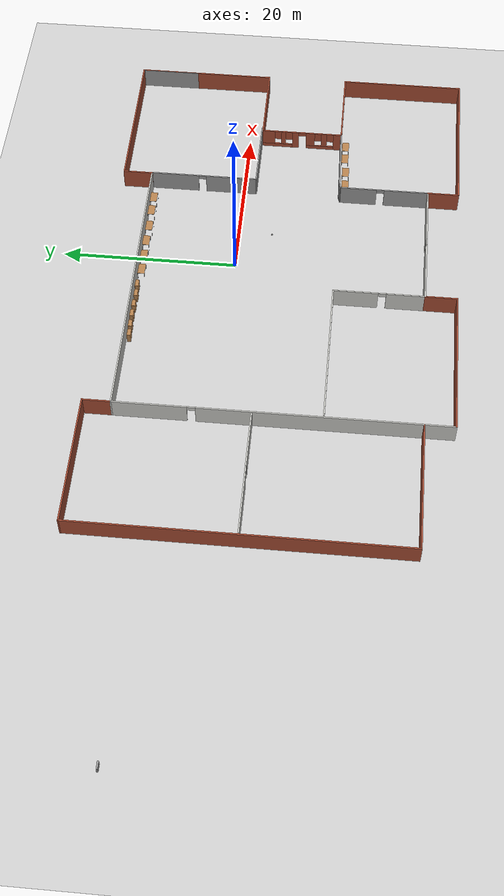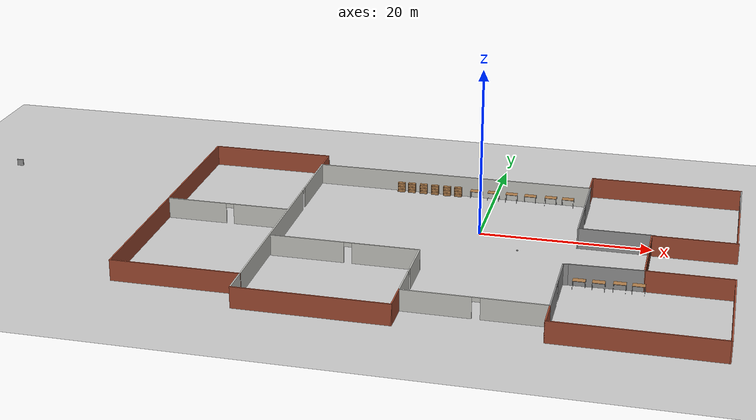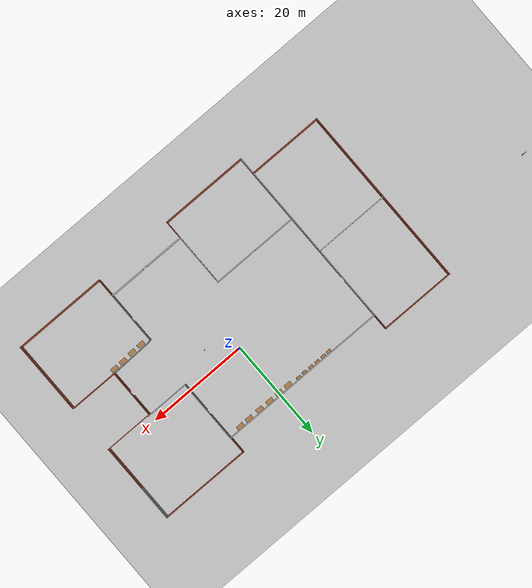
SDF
<sdf version="1.6">
 <world name="default">
  <model name="ground_plane">
   <static>1</static>
   <link name="link">
    <collision name="collision">
     <geometry><plane><normal>0 0 1</normal><size>100 100</size></plane></geometry>
     <surface><friction><ode><mu>100</mu><mu2>50</mu2></ode></friction></surface>
    </collision>
    <visual name="visual">
     <cast_shadows>0</cast_shadows>
     <geometry><plane><normal>0 0 1</normal><size>100 100</size></plane></geometry>
     <material>
      <script><uri>file://media/materials/scripts/gazebo.material</uri><name>Gazebo/Grey</name></script>
     </material>
    </visual>
   </link>
  </model>
  <light name="sun" type="directional">
   <pose>0 0 10 0 -0 0</pose>
   <diffuse>0.8 0.8 0.8 1</diffuse>
   <specular>0.1 0.1 0.1 1</specular>
   <attenuation>
    <range>1000</range>
    <constant>0.9</constant>
    <linear>0.01</linear>
    <quadratic>0.001</quadratic>
   </attenuation>
   <direction>-0.5 0.5 -1</direction>
  </light>
  <gravity>0 0 -9.8</gravity>
  <magnetic_field>6e-06 2.3e-05 -4.2e-05</magnetic_field>
  <atmosphere type="adiabatic"/>
  <physics name="default_physics" default="0" type="ode">
   <max_step_size>0.001</max_step_size>
   <real_time_factor>1</real_time_factor>
   <real_time_update_rate>1000</real_time_update_rate>
  </physics>
  <scene><ambient>0.4 0.4 0.4 1</ambient><background>0.7 0.7 0.7 1</background><shadows>1</shadows></scene>
  <spherical_coordinates>
   <surface_model>EARTH_WGS84</surface_model>
   <latitude_deg>0</latitude_deg>
   <longitude_deg>0</longitude_deg>
   <elevation>0</elevation>
   <heading_deg>0</heading_deg>
  </spherical_coordinates>
  <model name="Untitled">
   <link name="link_0">
    <inertial>
     <mass>1</mass>
     <inertia><ixx>0.1</ixx><ixy>0</ixy><ixz>0</ixz><iyy>0.1</iyy><iyz>0</iyz><izz>0.1</izz></inertia>
    </inertial>
    <visual name="visual">
     <geometry><sphere><radius>0.1</radius></sphere></geometry>
     <material>
      <lighting>1</lighting>
      <script><uri>file://media/materials/scripts/gazebo.material</uri><name>Gazebo/Grey</name></script>
      <ambient>1 1 1 1</ambient>
      <diffuse>1 1 1 1</diffuse>
      <specular>1 1 1 1</specular>
      <emissive>1 1 1 1</emissive>
      <shader type="vertex"><normal_map>__default__</normal_map></shader>
     </material>
    </visual>
    <collision name="collision">
     <geometry><sphere><radius>0.1</radius></sphere></geometry>
     <surface>
      <friction>
       <ode><mu>1</mu><mu2>1</mu2><fdir1>0 0 0</fdir1><slip1>0</slip1><slip2>0</slip2></ode>
       <torsional>
        <coefficient>1</coefficient>
        <patch_radius>0</patch_radius>
        <surface_radius>0</surface_radius>
        <use_patch_radius>1</use_patch_radius>
        <ode><slip>0</slip></ode>
       </torsional>
      </friction>
      <bounce><restitution_coefficient>0</restitution_coefficient><threshold>1e+06</threshold></bounce>
      <contact>
       <collide_without_contact>0</collide_without_contact>
       <collide_without_contact_bitmask>1</collide_without_contact_bitmask>
       <collide_bitmask>1</collide_bitmask>
       <ode>
        <soft_cfm>0</soft_cfm>
        <soft_erp>0.2</soft_erp>
        <kp>1e+13</kp>
        <kd>1</kd>
        <max_vel>0.01</max_vel>
        <min_depth>0</min_depth>
       </ode>
       <bullet>
        <split_impulse>1</split_impulse>
        <split_impulse_penetration_threshold>-0.01</split_impulse_penetration_threshold>
        <soft_cfm>0</soft_cfm>
        <soft_erp>0.2</soft_erp>
        <kp>1e+13</kp>
        <kd>1</kd>
       </bullet>
      </contact>
     </surface>
    </collision>
   </link>
   <static>0</static>
   <pose>5.06703 -3.86628 0.1 0 -0 0</pose>
  </model>
  <model name="building"><pose>-3.25886 19.1437 0 0 -0 0</pose><static>1</static></model>
  <model name="new_building_0">
   <pose>-3.7156 -5.49315 0 0 -0 0</pose>
   <link name="Wall_0">
    <pose>-18.35 -1.675 0 0 0 -1.5708</pose>
    <visual name="Wall_0_Visual_0">
     <pose>-14.2732 0 1.25 0 -0 0</pose>
     <geometry><box><size>8.20366 0.15 2.5</size></box></geometry>
     <material>
      <script><uri>file://media/materials/scripts/gazebo.material</uri><name>Gazebo/CeilingTiled</name></script>
      <ambient>1 1 1 1</ambient>
     </material>
    </visual>
    <collision name="Wall_0_Collision_0">
     <geometry><box><size>8.20366 0.15 2.5</size></box></geometry>
     <pose>-14.2732 0 1.25 0 -0 0</pose>
    </collision>
    <visual name="Wall_0_Visual_1">
     <pose>4.55183 0 1.25 0 -0 0</pose>
     <geometry><box><size>27.6463 0.15 2.5</size></box></geometry>
     <material>
      <script><uri>file://media/materials/scripts/gazebo.material</uri><name>Gazebo/CeilingTiled</name></script>
      <ambient>1 1 1 1</ambient>
     </material>
    </visual>
    <collision name="Wall_0_Collision_1">
     <geometry><box><size>27.6463 0.15 2.5</size></box></geometry>
     <pose>4.55183 0 1.25 0 -0 0</pose>
    </collision>
    <visual name="Wall_0_Visual_2">
     <pose>-9.72134 0 2.25 0 -0 0</pose>
     <geometry><box><size>0.9 0.15 0.5</size></box></geometry>
     <material>
      <script><uri>file://media/materials/scripts/gazebo.material</uri><name>Gazebo/CeilingTiled</name></script>
      <ambient>1 1 1 1</ambient>
     </material>
    </visual>
    <collision name="Wall_0_Collision_2">
     <geometry><box><size>0.9 0.15 0.5</size></box></geometry>
     <pose>-9.72134 0 2.25 0 -0 0</pose>
    </collision>
   </link>
   <link name="Wall_1">
    <collision name="Wall_1_Collision">
     <geometry><box><size>17.5 0.15 2.5</size></box></geometry>
     <pose>0 0 1.25 0 -0 0</pose>
    </collision>
    <visual name="Wall_1_Visual">
     <pose>0 0 1.25 0 -0 0</pose>
     <geometry><box><size>17.5 0.15 2.5</size></box></geometry>
     <material>
      <script><uri>file://media/materials/scripts/gazebo.material</uri><name>Gazebo/Bricks</name></script>
      <ambient>1 1 1 1</ambient>
     </material>
    </visual>
    <pose>-9.675 -19.975 0 0 -0 0</pose>
   </link>
   <link name="Wall_14">
    <collision name="Wall_14_Collision">
     <geometry><box><size>33.75 0.15 2.5</size></box></geometry>
     <pose>0 0 1.25 0 -0 0</pose>
    </collision>
    <visual name="Wall_14_Visual">
     <pose>0 0 1.25 0 -0 0</pose>
     <geometry><box><size>33.75 0.15 2.5</size></box></geometry>
     <material>
      <script><uri>file://media/materials/scripts/gazebo.material</uri><name>Gazebo/CeilingTiled</name></script>
      <ambient>1 1 1 1</ambient>
     </material>
    </visual>
    <pose>-1.55 16.625 0 0 -0 0</pose>
   </link>
   <link name="Wall_15">
    <collision name="Wall_15_Collision">
     <geometry><box><size>3.5 0.15 2.5</size></box></geometry>
     <pose>0 0 1.25 0 -0 0</pose>
    </collision>
    <visual name="Wall_15_Visual">
     <pose>0 0 1.25 0 -0 0</pose>
     <geometry><box><size>3.5 0.15 2.5</size></box></geometry>
     <material>
      <script><uri>file://media/materials/scripts/gazebo.material</uri><name>Gazebo/Bricks</name></script>
      <ambient>1 1 1 1</ambient>
     </material>
    </visual>
    <pose>15.25 18.3 0 0 -0 1.5708</pose>
   </link>
   <link name="Wall_16">
    <collision name="Wall_16_Collision">
     <geometry><box><size>18 0.15 2.5</size></box></geometry>
     <pose>0 0 1.25 0 -0 0</pose>
    </collision>
    <visual name="Wall_16_Visual">
     <pose>0 0 1.25 0 -0 0</pose>
     <geometry><box><size>18 0.15 2.5</size></box></geometry>
     <material>
      <script><uri>file://media/materials/scripts/gazebo.material</uri><name>Gazebo/Bricks</name></script>
      <ambient>1 1 1 1</ambient>
     </material>
    </visual>
    <pose>24.175 19.975 0 0 -0 0</pose>
   </link>
   <link name="Wall_17">
    <collision name="Wall_17_Collision">
     <geometry><box><size>7 0.15 2.5</size></box></geometry>
     <pose>0 0 1.25 0 -0 0</pose>
    </collision>
    <visual name="Wall_17_Visual">
     <pose>0 0 1.25 0 -0 0</pose>
     <geometry><box><size>7 0.15 2.5</size></box></geometry>
     <material>
      <script><uri>file://media/materials/scripts/gazebo.material</uri><name>Gazebo/Grey</name></script>
      <ambient>1 1 1 1</ambient>
     </material>
    </visual>
    <pose>33.1 16.55 0 0 0 -1.5708</pose>
   </link>
   <link name="Wall_19">
    <collision name="Wall_19_Collision">
     <geometry><box><size>16 0.15 2.5</size></box></geometry>
     <pose>0 0 1.25 0 -0 0</pose>
    </collision>
    <visual name="Wall_19_Visual">
     <pose>0 0 1.25 0 -0 0</pose>
     <geometry><box><size>16 0.15 2.5</size></box></geometry>
     <material>
      <script><uri>file://media/materials/scripts/gazebo.material</uri><name>Gazebo/Bricks</name></script>
      <ambient>1 1 1 1</ambient>
     </material>
    </visual>
    <pose>33.1 12.05 0 0 0 -1.5708</pose>
   </link>
   <link name="Wall_2">
    <collision name="Wall_2_Collision">
     <geometry><box><size>3.75 0.15 2.5</size></box></geometry>
     <pose>0 0 1.25 0 -0 0</pose>
    </collision>
    <visual name="Wall_2_Visual">
     <pose>0 0 1.25 0 -0 0</pose>
     <geometry><box><size>3.75 0.15 2.5</size></box></geometry>
     <material>
      <script><uri>file://media/materials/scripts/gazebo.material</uri><name>Gazebo/Bricks</name></script>
      <ambient>1 1 1 1</ambient>
     </material>
    </visual>
    <pose>-1 -18.175 0 0 -0 1.5708</pose>
   </link>
   <link name="Wall_23">
    <pose>-1 -11.2 0 0 -0 1.5708</pose>
    <visual name="Wall_23_Visual_0">
     <pose>-3.01613 0 1.25 0 -0 0</pose>
     <geometry><box><size>4.46774 0.15 2.5</size></box></geometry>
     <material>
      <script><uri>file://media/materials/scripts/gazebo.material</uri><name>Gazebo/CeilingTiled</name></script>
      <ambient>1 1 1 1</ambient>
     </material>
    </visual>
    <collision name="Wall_23_Collision_0">
     <geometry><box><size>4.46774 0.15 2.5</size></box></geometry>
     <pose>-3.01613 0 1.25 0 -0 0</pose>
    </collision>
    <visual name="Wall_23_Visual_1">
     <pose>2.68387 0 1.25 0 -0 0</pose>
     <geometry><box><size>5.13226 0.15 2.5</size></box></geometry>
     <material>
      <script><uri>file://media/materials/scripts/gazebo.material</uri><name>Gazebo/CeilingTiled</name></script>
      <ambient>1 1 1 1</ambient>
     </material>
    </visual>
    <collision name="Wall_23_Collision_1">
     <geometry><box><size>5.13226 0.15 2.5</size></box></geometry>
     <pose>2.68387 0 1.25 0 -0 0</pose>
    </collision>
    <visual name="Wall_23_Visual_2">
     <pose>-0.33226 0 2.25 0 -0 0</pose>
     <geometry><box><size>0.9 0.15 0.5</size></box></geometry>
     <material>
      <script><uri>file://media/materials/scripts/gazebo.material</uri><name>Gazebo/CeilingTiled</name></script>
      <ambient>1 1 1 1</ambient>
     </material>
    </visual>
    <collision name="Wall_23_Collision_2">
     <geometry><box><size>0.9 0.15 0.5</size></box></geometry>
     <pose>-0.33226 0 2.25 0 -0 0</pose>
    </collision>
   </link>
   <link name="Wall_24">
    <pose>-9.55 -6.025 0 0 -0 3.14159</pose>
    <visual name="Wall_24_Visual_0">
     <pose>-4.72507 0 1.25 0 -0 0</pose>
     <geometry><box><size>7.79986 0.15 2.5</size></box></geometry>
     <material>
      <script><uri>file://media/materials/scripts/gazebo.material</uri><name>Gazebo/CeilingTiled</name></script>
      <ambient>1 1 1 1</ambient>
     </material>
    </visual>
    <collision name="Wall_24_Collision_0">
     <geometry><box><size>7.79986 0.15 2.5</size></box></geometry>
     <pose>-4.72507 0 1.25 0 -0 0</pose>
    </collision>
    <visual name="Wall_24_Visual_1">
     <pose>4.34993 0 1.25 0 -0 0</pose>
     <geometry><box><size>8.55014 0.15 2.5</size></box></geometry>
     <material>
      <script><uri>file://media/materials/scripts/gazebo.material</uri><name>Gazebo/CeilingTiled</name></script>
      <ambient>1 1 1 1</ambient>
     </material>
    </visual>
    <collision name="Wall_24_Collision_1">
     <geometry><box><size>8.55014 0.15 2.5</size></box></geometry>
     <pose>4.34993 0 1.25 0 -0 0</pose>
    </collision>
    <visual name="Wall_24_Visual_2">
     <pose>-0.375141 0 2.25 0 -0 0</pose>
     <geometry><box><size>0.9 0.15 0.5</size></box></geometry>
     <material>
      <script><uri>file://media/materials/scripts/gazebo.material</uri><name>Gazebo/CeilingTiled</name></script>
      <ambient>1 1 1 1</ambient>
     </material>
    </visual>
    <collision name="Wall_24_Collision_2">
     <geometry><box><size>0.9 0.15 0.5</size></box></geometry>
     <pose>-0.375141 0 2.25 0 -0 0</pose>
    </collision>
   </link>
   <link name="Wall_26">
    <collision name="Wall_26_Collision">
     <geometry><box><size>3.25 0.15 2.5</size></box></geometry>
     <pose>0 0 1.25 0 -0 0</pose>
    </collision>
    <visual name="Wall_26_Visual">
     <pose>0 0 1.25 0 -0 0</pose>
     <geometry><box><size>3.25 0.15 2.5</size></box></geometry>
     <material>
      <script><uri>file://media/materials/scripts/gazebo.material</uri><name>Gazebo/Bricks</name></script>
      <ambient>1 1 1 1</ambient>
     </material>
    </visual>
    <pose>-18.35 18.175 0 0 -0 1.5708</pose>
   </link>
   <link name="Wall_27">
    <collision name="Wall_27_Collision">
     <geometry><box><size>15 0.15 2.5</size></box></geometry>
     <pose>0 0 1.25 0 -0 0</pose>
    </collision>
    <visual name="Wall_27_Visual">
     <pose>0 0 1.25 0 -0 0</pose>
     <geometry><box><size>15 0.15 2.5</size></box></geometry>
     <material>
      <script><uri>file://media/materials/scripts/gazebo.material</uri><name>Gazebo/Bricks</name></script>
      <ambient>1 1 1 1</ambient>
     </material>
    </visual>
    <pose>-25.775 19.725 0 0 -0 3.14159</pose>
   </link>
   <link name="Wall_28">
    <collision name="Wall_28_Collision">
     <geometry><box><size>36.5 0.15 2.5</size></box></geometry>
     <pose>0 0 1.25 0 -0 0</pose>
    </collision>
    <visual name="Wall_28_Visual">
     <pose>0 0 1.25 0 -0 0</pose>
     <geometry><box><size>36.5 0.15 2.5</size></box></geometry>
     <material>
      <script><uri>file://media/materials/scripts/gazebo.material</uri><name>Gazebo/Bricks</name></script>
      <ambient>1 1 1 1</ambient>
     </material>
    </visual>
    <pose>-33.2 1.55 0 0 0 -1.5708</pose>
   </link>
   <link name="Wall_29">
    <collision name="Wall_29_Collision">
     <geometry><box><size>15 0.15 2.5</size></box></geometry>
     <pose>0 0 1.25 0 -0 0</pose>
    </collision>
    <visual name="Wall_29_Visual">
     <pose>0 0 1.25 0 -0 0</pose>
     <geometry><box><size>15 0.15 2.5</size></box></geometry>
     <material>
      <script><uri>file://media/materials/scripts/gazebo.material</uri><name>Gazebo/Bricks</name></script>
      <ambient>1 1 1 1</ambient>
     </material>
    </visual>
    <pose>-25.775 -16.625 0 0 -0 0</pose>
   </link>
   <link name="Wall_3">
    <pose>6.925 -16.375 0 0 -0 0</pose>
    <visual name="Wall_3_Visual_0">
     <pose>-4.08922 0 1.25 0 -0 0</pose>
     <geometry><box><size>7.82155 0.15 2.5</size></box></geometry>
     <material>
      <script><uri>file://media/materials/scripts/gazebo.material</uri><name>Gazebo/CeilingTiled</name></script>
      <ambient>1 1 1 1</ambient>
     </material>
    </visual>
    <collision name="Wall_3_Collision_0">
     <geometry><box><size>7.82155 0.15 2.5</size></box></geometry>
     <pose>-4.08922 0 1.25 0 -0 0</pose>
    </collision>
    <visual name="Wall_3_Visual_1">
     <pose>4.36078 0 1.25 0 -0 0</pose>
     <geometry><box><size>7.27845 0.15 2.5</size></box></geometry>
     <material>
      <script><uri>file://media/materials/scripts/gazebo.material</uri><name>Gazebo/CeilingTiled</name></script>
      <ambient>1 1 1 1</ambient>
     </material>
    </visual>
    <collision name="Wall_3_Collision_1">
     <geometry><box><size>7.27845 0.15 2.5</size></box></geometry>
     <pose>4.36078 0 1.25 0 -0 0</pose>
    </collision>
    <visual name="Wall_3_Visual_2">
     <pose>0.271553 0 2.25 0 -0 0</pose>
     <geometry><box><size>0.9 0.15 0.5</size></box></geometry>
     <material>
      <script><uri>file://media/materials/scripts/gazebo.material</uri><name>Gazebo/CeilingTiled</name></script>
      <ambient>1 1 1 1</ambient>
     </material>
    </visual>
    <collision name="Wall_3_Collision_2">
     <geometry><box><size>0.9 0.15 0.5</size></box></geometry>
     <pose>0.271553 0 2.25 0 -0 0</pose>
    </collision>
   </link>
   <link name="Wall_31">
    <pose>-25.8582 1.59648 0 0 -0 0</pose>
    <visual name="Wall_31_Visual_0">
     <pose>-3.74225 0 1.25 0 -0 0</pose>
     <geometry><box><size>7.2655 0.15 2.5</size></box></geometry>
     <material>
      <script><uri>file://media/materials/scripts/gazebo.material</uri><name>Gazebo/CeilingTiled</name></script>
      <ambient>1 1 1 1</ambient>
     </material>
    </visual>
    <collision name="Wall_31_Collision_0">
     <geometry><box><size>7.2655 0.15 2.5</size></box></geometry>
     <pose>-3.74225 0 1.25 0 -0 0</pose>
    </collision>
    <visual name="Wall_31_Visual_1">
     <pose>4.08275 0 1.25 0 -0 0</pose>
     <geometry><box><size>6.5845 0.15 2.5</size></box></geometry>
     <material>
      <script><uri>file://media/materials/scripts/gazebo.material</uri><name>Gazebo/CeilingTiled</name></script>
      <ambient>1 1 1 1</ambient>
     </material>
    </visual>
    <collision name="Wall_31_Collision_1">
     <geometry><box><size>6.5845 0.15 2.5</size></box></geometry>
     <pose>4.08275 0 1.25 0 -0 0</pose>
    </collision>
    <visual name="Wall_31_Visual_2">
     <pose>0.340496 0 2.25 0 -0 0</pose>
     <geometry><box><size>0.9 0.15 0.5</size></box></geometry>
     <material>
      <script><uri>file://media/materials/scripts/gazebo.material</uri><name>Gazebo/CeilingTiled</name></script>
      <ambient>1 1 1 1</ambient>
     </material>
    </visual>
    <collision name="Wall_31_Collision_2">
     <geometry><box><size>0.9 0.15 0.5</size></box></geometry>
     <pose>0.340496 0 2.25 0 -0 0</pose>
    </collision>
   </link>
   <link name="Wall_34">
    <pose>14.85 -11.2 0 0 -0 1.5708</pose>
    <visual name="Wall_34_Visual_0">
     <pose>-2.62042 0 1.25 0 -0 0</pose>
     <geometry><box><size>5.25915 0.15 2.5</size></box></geometry>
     <material>
      <script><uri>file://media/materials/scripts/gazebo.material</uri><name>Gazebo/Grey</name></script>
      <ambient>1 1 1 1</ambient>
     </material>
    </visual>
    <collision name="Wall_34_Collision_0">
     <geometry><box><size>5.25915 0.15 2.5</size></box></geometry>
     <pose>-2.62042 0 1.25 0 -0 0</pose>
    </collision>
    <visual name="Wall_34_Visual_1">
     <pose>3.07958 0 1.25 0 -0 0</pose>
     <geometry><box><size>4.34084 0.15 2.5</size></box></geometry>
     <material>
      <script><uri>file://media/materials/scripts/gazebo.material</uri><name>Gazebo/Grey</name></script>
      <ambient>1 1 1 1</ambient>
     </material>
    </visual>
    <collision name="Wall_34_Collision_1">
     <geometry><box><size>4.34084 0.15 2.5</size></box></geometry>
     <pose>3.07958 0 1.25 0 -0 0</pose>
    </collision>
    <visual name="Wall_34_Visual_2">
     <pose>0.459155 0 2.25 0 -0 0</pose>
     <geometry><box><size>0.9 0.15 0.5</size></box></geometry>
     <material>
      <script><uri>file://media/materials/scripts/gazebo.material</uri><name>Gazebo/Grey</name></script>
      <ambient>1 1 1 1</ambient>
     </material>
    </visual>
    <collision name="Wall_34_Collision_2">
     <geometry><box><size>0.9 0.15 0.5</size></box></geometry>
     <pose>0.459155 0 2.25 0 -0 0</pose>
    </collision>
   </link>
   <link name="Wall_35">
    <collision name="Wall_35_Collision">
     <geometry><box><size>0.75 0.15 2.5</size></box></geometry>
     <pose>0 0 1.25 0 -0 0</pose>
    </collision>
    <visual name="Wall_35_Visual">
     <pose>0 0 1.25 0 -0 0</pose>
     <geometry><box><size>0.75 0.15 2.5</size></box></geometry>
     <material>
      <script><uri>file://media/materials/scripts/gazebo.material</uri><name>Gazebo/Grey</name></script>
      <ambient>1 1 1 1</ambient>
     </material>
    </visual>
    <pose>15.1398 -5.94735 0 0 -0 0.261799</pose>
   </link>
   <link name="Wall_36">
    <collision name="Wall_36_Collision">
     <geometry><box><size>8.32411 0.15 2.5</size></box></geometry>
     <pose>0 0 1.25 0 -0 0</pose>
    </collision>
    <visual name="Wall_36_Visual">
     <pose>0 0 1.25 0 -0 0</pose>
     <geometry><box><size>8.32411 0.15 2.5</size></box></geometry>
     <material>
      <script><uri>file://media/materials/scripts/gazebo.material</uri><name>Gazebo/Grey</name></script>
      <ambient>1 1 1 1</ambient>
     </material>
    </visual>
    <pose>19.5148 -5.74735 0 0 -0 0.029942</pose>
   </link>
   <link name="Wall_38">
    <collision name="Wall_38_Collision">
     <geometry><box><size>8.75 0.15 2.5</size></box></geometry>
     <pose>0 0 1.25 0 -0 0</pose>
    </collision>
    <visual name="Wall_38_Visual">
     <pose>0 0 1.25 0 -0 0</pose>
     <geometry><box><size>8.75 0.15 2.5</size></box></geometry>
     <material>
      <script><uri>file://media/materials/scripts/gazebo.material</uri><name>Gazebo/Grey</name></script>
      <ambient>1 1 1 1</ambient>
     </material>
    </visual>
    <pose>19.607 4.1097 0 0 -0 3.14159</pose>
   </link>
   <link name="Wall_39">
    <pose>15.307 10.4097 0 0 -0 1.5708</pose>
    <visual name="Wall_39_Visual_0">
     <pose>-3.34488 0 1.25 0 -0 0</pose>
     <geometry><box><size>6.06024 0.15 2.5</size></box></geometry>
     <material>
      <script><uri>file://media/materials/scripts/gazebo.material</uri><name>Gazebo/Grey</name></script>
      <ambient>1 1 1 1</ambient>
     </material>
    </visual>
    <collision name="Wall_39_Collision_0">
     <geometry><box><size>6.06024 0.15 2.5</size></box></geometry>
     <pose>-3.34488 0 1.25 0 -0 0</pose>
    </collision>
    <visual name="Wall_39_Visual_1">
     <pose>3.48012 0 1.25 0 -0 0</pose>
     <geometry><box><size>5.78976 0.15 2.5</size></box></geometry>
     <material>
      <script><uri>file://media/materials/scripts/gazebo.material</uri><name>Gazebo/Grey</name></script>
      <ambient>1 1 1 1</ambient>
     </material>
    </visual>
    <collision name="Wall_39_Collision_1">
     <geometry><box><size>5.78976 0.15 2.5</size></box></geometry>
     <pose>3.48012 0 1.25 0 -0 0</pose>
    </collision>
    <visual name="Wall_39_Visual_2">
     <pose>0.135236 0 2.25 0 -0 0</pose>
     <geometry><box><size>0.9 0.15 0.5</size></box></geometry>
     <material>
      <script><uri>file://media/materials/scripts/gazebo.material</uri><name>Gazebo/Grey</name></script>
      <ambient>1 1 1 1</ambient>
     </material>
    </visual>
    <collision name="Wall_39_Collision_2">
     <geometry><box><size>0.9 0.15 0.5</size></box></geometry>
     <pose>0.135236 0 2.25 0 -0 0</pose>
    </collision>
   </link>
   <link name="Wall_4">
    <collision name="Wall_4_Collision">
     <geometry><box><size>3.75 0.15 2.5</size></box></geometry>
     <pose>0 0 1.25 0 -0 0</pose>
    </collision>
    <visual name="Wall_4_Visual">
     <pose>0 0 1.25 0 -0 0</pose>
     <geometry><box><size>3.75 0.15 2.5</size></box></geometry>
     <material>
      <script><uri>file://media/materials/scripts/gazebo.material</uri><name>Gazebo/Bricks</name></script>
      <ambient>1 1 1 1</ambient>
     </material>
    </visual>
    <pose>14.85 -18.175 0 0 0 -1.5708</pose>
   </link>
   <link name="Wall_5">
    <collision name="Wall_5_Collision">
     <geometry><box><size>18.5 0.15 2.5</size></box></geometry>
     <pose>0 0 1.25 0 -0 0</pose>
    </collision>
    <visual name="Wall_5_Visual">
     <pose>0 0 1.25 0 -0 0</pose>
     <geometry><box><size>18.5 0.15 2.5</size></box></geometry>
     <material>
      <script><uri>file://media/materials/scripts/gazebo.material</uri><name>Gazebo/Bricks</name></script>
      <ambient>1 1 1 1</ambient>
     </material>
    </visual>
    <pose>24.025 -19.975 0 0 -0 0</pose>
   </link>
   <link name="Wall_6">
    <collision name="Wall_6_Collision">
     <geometry><box><size>14.5 0.15 2.5</size></box></geometry>
     <pose>0 0 1.25 0 -0 0</pose>
    </collision>
    <visual name="Wall_6_Visual">
     <pose>0 0 1.25 0 -0 0</pose>
     <geometry><box><size>14.5 0.15 2.5</size></box></geometry>
     <material>
      <script><uri>file://media/materials/scripts/gazebo.material</uri><name>Gazebo/Bricks</name></script>
      <ambient>1 1 1 1</ambient>
     </material>
    </visual>
    <pose>33.2 -12.8 0 0 -0 1.5708</pose>
   </link>
   <link name="Wall_7">
    <collision name="Wall_7_Collision">
     <geometry><box><size>9.75 0.15 2.5</size></box></geometry>
     <pose>0 0 1.25 0 -0 0</pose>
    </collision>
    <visual name="Wall_7_Visual">
     <pose>0 0 1.25 0 -0 0</pose>
     <geometry><box><size>9.75 0.15 2.5</size></box></geometry>
     <material>
      <script><uri>file://media/materials/scripts/gazebo.material</uri><name>Gazebo/Bricks</name></script>
      <ambient>1 1 1 1</ambient>
     </material>
    </visual>
    <pose>28.4 -5.625 0 0 -0 3.14159</pose>
   </link>
   <link name="Wall_8">
    <pose>23.6 -0.825 0 0 -0 1.5708</pose>
    <visual name="Wall_8_Visual_0">
     <pose>-4.35769 0 1.25 0 -0 0</pose>
     <geometry><box><size>1.03461 0.15 2.5</size></box></geometry>
     <material>
      <script><uri>file://media/materials/scripts/gazebo.material</uri><name>Gazebo/Bricks</name></script>
      <ambient>1 1 1 1</ambient>
     </material>
    </visual>
    <collision name="Wall_8_Collision_0">
     <geometry><box><size>1.03461 0.15 2.5</size></box></geometry>
     <pose>-4.35769 0 1.25 0 -0 0</pose>
    </collision>
    <visual name="Wall_8_Visual_1">
     <pose>0.789877 0 1.25 0 -0 0</pose>
     <geometry><box><size>0.786971 0.15 2.5</size></box></geometry>
     <material>
      <script><uri>file://media/materials/scripts/gazebo.material</uri><name>Gazebo/Bricks</name></script>
      <ambient>1 1 1 1</ambient>
     </material>
    </visual>
    <collision name="Wall_8_Collision_1">
     <geometry><box><size>0.786971 0.15 2.5</size></box></geometry>
     <pose>0.789877 0 1.25 0 -0 0</pose>
    </collision>
    <visual name="Wall_8_Visual_2">
     <pose>-2.172 0 0.25 0 -0 0</pose>
     <geometry><box><size>3.33678 0.15 0.5</size></box></geometry>
     <material>
      <script><uri>file://media/materials/scripts/gazebo.material</uri><name>Gazebo/Bricks</name></script>
      <ambient>1 1 1 1</ambient>
     </material>
    </visual>
    <collision name="Wall_8_Collision_2">
     <geometry><box><size>3.33678 0.15 0.5</size></box></geometry>
     <pose>-2.172 0 0.25 0 -0 0</pose>
    </collision>
    <visual name="Wall_8_Visual_3">
     <pose>3.02918 0 0.25 0 -0 0</pose>
     <geometry><box><size>3.69164 0.15 0.5</size></box></geometry>
     <material>
      <script><uri>file://media/materials/scripts/gazebo.material</uri><name>Gazebo/Bricks</name></script>
      <ambient>1 1 1 1</ambient>
     </material>
    </visual>
    <collision name="Wall_8_Collision_3">
     <geometry><box><size>3.69164 0.15 0.5</size></box></geometry>
     <pose>3.02918 0 0.25 0 -0 0</pose>
    </collision>
    <visual name="Wall_8_Visual_4">
     <pose>-2.69744 0 1.5 0 -0 0</pose>
     <geometry><box><size>0.685898 0.15 2</size></box></geometry>
     <material>
      <script><uri>file://media/materials/scripts/gazebo.material</uri><name>Gazebo/Bricks</name></script>
      <ambient>1 1 1 1</ambient>
     </material>
    </visual>
    <collision name="Wall_8_Collision_4">
     <geometry><box><size>0.685898 0.15 2</size></box></geometry>
     <pose>-2.69744 0 1.5 0 -0 0</pose>
    </collision>
    <visual name="Wall_8_Visual_5">
     <pose>-1.02905 0 1.5 0 -0 0</pose>
     <geometry><box><size>1.05088 0.15 2</size></box></geometry>
     <material>
      <script><uri>file://media/materials/scripts/gazebo.material</uri><name>Gazebo/Bricks</name></script>
      <ambient>1 1 1 1</ambient>
     </material>
    </visual>
    <collision name="Wall_8_Collision_5">
     <geometry><box><size>1.05088 0.15 2</size></box></geometry>
     <pose>-1.02905 0 1.5 0 -0 0</pose>
    </collision>
    <visual name="Wall_8_Visual_6">
     <pose>-1.02905 0 1.5 0 -0 0</pose>
     <geometry><box><size>1.05088 0.15 2</size></box></geometry>
     <material>
      <script><uri>file://media/materials/scripts/gazebo.material</uri><name>Gazebo/Bricks</name></script>
      <ambient>1 1 1 1</ambient>
     </material>
    </visual>
    <collision name="Wall_8_Collision_6">
     <geometry><box><size>1.05088 0.15 2</size></box></geometry>
     <pose>-1.02905 0 1.5 0 -0 0</pose>
    </collision>
    <visual name="Wall_8_Visual_7">
     <pose>2.25555 0 1.5 0 -0 0</pose>
     <geometry><box><size>0.544384 0.15 2</size></box></geometry>
     <material>
      <script><uri>file://media/materials/scripts/gazebo.material</uri><name>Gazebo/Bricks</name></script>
      <ambient>1 1 1 1</ambient>
     </material>
    </visual>
    <collision name="Wall_8_Collision_7">
     <geometry><box><size>0.544384 0.15 2</size></box></geometry>
     <pose>2.25555 0 1.5 0 -0 0</pose>
    </collision>
    <visual name="Wall_8_Visual_8">
     <pose>4.10137 0 1.5 0 -0 0</pose>
     <geometry><box><size>1.54725 0.15 2</size></box></geometry>
     <material>
      <script><uri>file://media/materials/scripts/gazebo.material</uri><name>Gazebo/Bricks</name></script>
      <ambient>1 1 1 1</ambient>
     </material>
    </visual>
    <collision name="Wall_8_Collision_8">
     <geometry><box><size>1.54725 0.15 2</size></box></geometry>
     <pose>4.10137 0 1.5 0 -0 0</pose>
    </collision>
    <visual name="Wall_8_Visual_9">
     <pose>-3.44039 0 1.9 0 -0 0</pose>
     <geometry><box><size>0.8 0.15 1.2</size></box></geometry>
     <material>
      <script><uri>file://media/materials/scripts/gazebo.material</uri><name>Gazebo/Bricks</name></script>
      <ambient>1 1 1 1</ambient>
     </material>
    </visual>
    <collision name="Wall_8_Collision_9">
     <geometry><box><size>0.8 0.15 1.2</size></box></geometry>
     <pose>-3.44039 0 1.9 0 -0 0</pose>
    </collision>
    <visual name="Wall_8_Visual_10">
     <pose>1.58336 0 1.9 0 -0 0</pose>
     <geometry><box><size>0.8 0.15 1.2</size></box></geometry>
     <material>
      <script><uri>file://media/materials/scripts/gazebo.material</uri><name>Gazebo/Bricks</name></script>
      <ambient>1 1 1 1</ambient>
     </material>
    </visual>
    <collision name="Wall_8_Collision_10">
     <geometry><box><size>0.8 0.15 1.2</size></box></geometry>
     <pose>1.58336 0 1.9 0 -0 0</pose>
    </collision>
    <visual name="Wall_8_Visual_11">
     <pose>-1.95449 0 1.9 0 -0 0</pose>
     <geometry><box><size>0.8 0.15 1.2</size></box></geometry>
     <material>
      <script><uri>file://media/materials/scripts/gazebo.material</uri><name>Gazebo/Bricks</name></script>
      <ambient>1 1 1 1</ambient>
     </material>
    </visual>
    <collision name="Wall_8_Collision_11">
     <geometry><box><size>0.8 0.15 1.2</size></box></geometry>
     <pose>-1.95449 0 1.9 0 -0 0</pose>
    </collision>
    <visual name="Wall_8_Visual_12">
     <pose>2.92775 0 1.9 0 -0 0</pose>
     <geometry><box><size>0.8 0.15 1.2</size></box></geometry>
     <material>
      <script><uri>file://media/materials/scripts/gazebo.material</uri><name>Gazebo/Bricks</name></script>
      <ambient>1 1 1 1</ambient>
     </material>
    </visual>
    <collision name="Wall_8_Collision_12">
     <geometry><box><size>0.8 0.15 1.2</size></box></geometry>
     <pose>2.92775 0 1.9 0 -0 0</pose>
    </collision>
    <visual name="Wall_8_Visual_13">
     <pose>-0.053609 0 2.25 0 -0 0</pose>
     <geometry><box><size>0.9 0.15 0.5</size></box></geometry>
     <material>
      <script><uri>file://media/materials/scripts/gazebo.material</uri><name>Gazebo/Bricks</name></script>
      <ambient>1 1 1 1</ambient>
     </material>
    </visual>
    <collision name="Wall_8_Collision_13">
     <geometry><box><size>0.9 0.15 0.5</size></box></geometry>
     <pose>-0.053609 0 2.25 0 -0 0</pose>
    </collision>
    <visual name="Wall_8_Visual_14">
     <pose>-0.053609 0 2.25 0 -0 0</pose>
     <geometry><box><size>0.9 0.15 0.5</size></box></geometry>
     <material>
      <script><uri>file://media/materials/scripts/gazebo.material</uri><name>Gazebo/Bricks</name></script>
      <ambient>1 1 1 1</ambient>
     </material>
    </visual>
    <collision name="Wall_8_Collision_14">
     <geometry><box><size>0.9 0.15 0.5</size></box></geometry>
     <pose>-0.053609 0 2.25 0 -0 0</pose>
    </collision>
   </link>
   <link name="Wall_9">
    <collision name="Wall_9_Collision">
     <geometry><box><size>9.75 0.15 2.5</size></box></geometry>
     <pose>0 0 1.25 0 -0 0</pose>
    </collision>
    <visual name="Wall_9_Visual">
     <pose>0 0 1.25 0 -0 0</pose>
     <geometry><box><size>9.75 0.15 2.5</size></box></geometry>
     <material>
      <script><uri>file://media/materials/scripts/gazebo.material</uri><name>Gazebo/Bricks</name></script>
      <ambient>1 1 1 1</ambient>
     </material>
    </visual>
    <pose>28.4 3.975 0 0 -0 0</pose>
   </link>
   <link name="Window_4">
    <collision name="Window_4_Collision">
     <geometry><box><size>0.8 0.17 0.8</size></box></geometry>
     <pose>0 0 0.4 0 -0 0</pose>
    </collision>
    <visual name="Window_4_Visual">
     <pose>0 0 0.4 0 -0 0</pose>
     <geometry><box><size>0.8 0.17 0.8</size></box></geometry>
     <material>
      <script><uri>file://media/materials/scripts/gazebo.material</uri><name>Gazebo/Grey</name></script>
     </material>
    </visual>
    <pose>-57.4661 12.0612 0.5 0 -0 0</pose>
   </link>
   <static>1</static>
  </model>
  <model name="bookshelf">
   <static>1</static>
   <link name="link">
    <inertial><mass>1</mass></inertial>
    <collision name="back">
     <pose>0 0.005 0.6 0 -0 0</pose>
     <geometry><box><size>0.9 0.01 1.2</size></box></geometry>
    </collision>
    <visual name="visual1">
     <pose>0 0.005 0.6 0 -0 0</pose>
     <geometry><box><size>0.9 0.01 1.2</size></box></geometry>
     <material>
      <script><uri>file://media/materials/scripts/gazebo.material</uri><name>Gazebo/Wood</name></script>
     </material>
    </visual>
    <collision name="left_side">
     <pose>0.45 -0.195 0.6 0 -0 0</pose>
     <geometry><box><size>0.02 0.4 1.2</size></box></geometry>
    </collision>
    <visual name="visual2">
     <pose>0.45 -0.195 0.6 0 -0 0</pose>
     <geometry><box><size>0.02 0.4 1.2</size></box></geometry>
     <material>
      <script><uri>file://media/materials/scripts/gazebo.material</uri><name>Gazebo/Wood</name></script>
     </material>
    </visual>
    <collision name="right_side">
     <pose>-0.45 -0.195 0.6 0 -0 0</pose>
     <geometry><box><size>0.02 0.4 1.2</size></box></geometry>
    </collision>
    <visual name="visual3">
     <pose>-0.45 -0.195 0.6 0 -0 0</pose>
     <geometry><box><size>0.02 0.4 1.2</size></box></geometry>
     <material>
      <script><uri>file://media/materials/scripts/gazebo.material</uri><name>Gazebo/Wood</name></script>
     </material>
    </visual>
    <collision name="bottom">
     <pose>0 -0.195 0.03 0 -0 0</pose>
     <geometry><box><size>0.88 0.4 0.06</size></box></geometry>
    </collision>
    <visual name="visual4">
     <pose>0 -0.195 0.03 0 -0 0</pose>
     <geometry><box><size>0.88 0.4 0.06</size></box></geometry>
     <material>
      <script><uri>file://media/materials/scripts/gazebo.material</uri><name>Gazebo/Wood</name></script>
     </material>
    </visual>
    <collision name="top">
     <pose>0 -0.195 1.19 0 -0 0</pose>
     <geometry><box><size>0.88 0.4 0.02</size></box></geometry>
    </collision>
    <visual name="visual5">
     <pose>0 -0.195 1.19 0 -0 0</pose>
     <geometry><box><size>0.88 0.4 0.02</size></box></geometry>
     <material>
      <script><uri>file://media/materials/scripts/gazebo.material</uri><name>Gazebo/Wood</name></script>
     </material>
    </visual>
    <collision name="low_shelf">
     <pose>0 -0.195 0.43 0 -0 0</pose>
     <geometry><box><size>0.88 0.4 0.02</size></box></geometry>
    </collision>
    <visual name="visual6">
     <pose>0 -0.195 0.43 0 -0 0</pose>
     <geometry><box><size>0.88 0.4 0.02</size></box></geometry>
     <material>
      <script><uri>file://media/materials/scripts/gazebo.material</uri><name>Gazebo/Wood</name></script>
     </material>
    </visual>
    <collision name="high_shelf">
     <pose>0 -0.195 0.8 0 -0 0</pose>
     <geometry><box><size>0.88 0.4 0.02</size></box></geometry>
    </collision>
    <visual name="visual7">
     <pose>0 -0.195 0.8 0 -0 0</pose>
     <geometry><box><size>0.88 0.4 0.02</size></box></geometry>
     <material>
      <script><uri>file://media/materials/scripts/gazebo.material</uri><name>Gazebo/Wood</name></script>
     </material>
    </visual>
   </link>
   <pose>-10.3744 10.9607 0 0 -0 0</pose>
  </model>
  <model name="bookshelf_clone">
   <static>1</static>
   <link name="link">
    <inertial><mass>1</mass></inertial>
    <collision name="back">
     <pose>0 0.005 0.6 0 -0 0</pose>
     <geometry><box><size>0.9 0.01 1.2</size></box></geometry>
    </collision>
    <visual name="visual1">
     <pose>0 0.005 0.6 0 -0 0</pose>
     <geometry><box><size>0.9 0.01 1.2</size></box></geometry>
     <material>
      <script><uri>file://media/materials/scripts/gazebo.material</uri><name>Gazebo/Wood</name></script>
     </material>
    </visual>
    <collision name="left_side">
     <pose>0.45 -0.195 0.6 0 -0 0</pose>
     <geometry><box><size>0.02 0.4 1.2</size></box></geometry>
    </collision>
    <visual name="visual2">
     <pose>0.45 -0.195 0.6 0 -0 0</pose>
     <geometry><box><size>0.02 0.4 1.2</size></box></geometry>
     <material>
      <script><uri>file://media/materials/scripts/gazebo.material</uri><name>Gazebo/Wood</name></script>
     </material>
    </visual>
    <collision name="right_side">
     <pose>-0.45 -0.195 0.6 0 -0 0</pose>
     <geometry><box><size>0.02 0.4 1.2</size></box></geometry>
    </collision>
    <visual name="visual3">
     <pose>-0.45 -0.195 0.6 0 -0 0</pose>
     <geometry><box><size>0.02 0.4 1.2</size></box></geometry>
     <material>
      <script><uri>file://media/materials/scripts/gazebo.material</uri><name>Gazebo/Wood</name></script>
     </material>
    </visual>
    <collision name="bottom">
     <pose>0 -0.195 0.03 0 -0 0</pose>
     <geometry><box><size>0.88 0.4 0.06</size></box></geometry>
    </collision>
    <visual name="visual4">
     <pose>0 -0.195 0.03 0 -0 0</pose>
     <geometry><box><size>0.88 0.4 0.06</size></box></geometry>
     <material>
      <script><uri>file://media/materials/scripts/gazebo.material</uri><name>Gazebo/Wood</name></script>
     </material>
    </visual>
    <collision name="top">
     <pose>0 -0.195 1.19 0 -0 0</pose>
     <geometry><box><size>0.88 0.4 0.02</size></box></geometry>
    </collision>
    <visual name="visual5">
     <pose>0 -0.195 1.19 0 -0 0</pose>
     <geometry><box><size>0.88 0.4 0.02</size></box></geometry>
     <material>
      <script><uri>file://media/materials/scripts/gazebo.material</uri><name>Gazebo/Wood</name></script>
     </material>
    </visual>
    <collision name="low_shelf">
     <pose>0 -0.195 0.43 0 -0 0</pose>
     <geometry><box><size>0.88 0.4 0.02</size></box></geometry>
    </collision>
    <visual name="visual6">
     <pose>0 -0.195 0.43 0 -0 0</pose>
     <geometry><box><size>0.88 0.4 0.02</size></box></geometry>
     <material>
      <script><uri>file://media/materials/scripts/gazebo.material</uri><name>Gazebo/Wood</name></script>
     </material>
    </visual>
    <collision name="high_shelf">
     <pose>0 -0.195 0.8 0 -0 0</pose>
     <geometry><box><size>0.88 0.4 0.02</size></box></geometry>
    </collision>
    <visual name="visual7">
     <pose>0 -0.195 0.8 0 -0 0</pose>
     <geometry><box><size>0.88 0.4 0.02</size></box></geometry>
     <material>
      <script><uri>file://media/materials/scripts/gazebo.material</uri><name>Gazebo/Wood</name></script>
     </material>
    </visual>
   </link>
   <pose>-8.909 10.9943 0 0 -0 0</pose>
  </model>
  <model name="bookshelf_clone_0">
   <static>1</static>
   <link name="link">
    <inertial><mass>1</mass></inertial>
    <collision name="back">
     <pose>0 0.005 0.6 0 -0 0</pose>
     <geometry><box><size>0.9 0.01 1.2</size></box></geometry>
    </collision>
    <visual name="visual1">
     <pose>0 0.005 0.6 0 -0 0</pose>
     <geometry><box><size>0.9 0.01 1.2</size></box></geometry>
     <material>
      <script><uri>file://media/materials/scripts/gazebo.material</uri><name>Gazebo/Wood</name></script>
     </material>
    </visual>
    <collision name="left_side">
     <pose>0.45 -0.195 0.6 0 -0 0</pose>
     <geometry><box><size>0.02 0.4 1.2</size></box></geometry>
    </collision>
    <visual name="visual2">
     <pose>0.45 -0.195 0.6 0 -0 0</pose>
     <geometry><box><size>0.02 0.4 1.2</size></box></geometry>
     <material>
      <script><uri>file://media/materials/scripts/gazebo.material</uri><name>Gazebo/Wood</name></script>
     </material>
    </visual>
    <collision name="right_side">
     <pose>-0.45 -0.195 0.6 0 -0 0</pose>
     <geometry><box><size>0.02 0.4 1.2</size></box></geometry>
    </collision>
    <visual name="visual3">
     <pose>-0.45 -0.195 0.6 0 -0 0</pose>
     <geometry><box><size>0.02 0.4 1.2</size></box></geometry>
     <material>
      <script><uri>file://media/materials/scripts/gazebo.material</uri><name>Gazebo/Wood</name></script>
     </material>
    </visual>
    <collision name="bottom">
     <pose>0 -0.195 0.03 0 -0 0</pose>
     <geometry><box><size>0.88 0.4 0.06</size></box></geometry>
    </collision>
    <visual name="visual4">
     <pose>0 -0.195 0.03 0 -0 0</pose>
     <geometry><box><size>0.88 0.4 0.06</size></box></geometry>
     <material>
      <script><uri>file://media/materials/scripts/gazebo.material</uri><name>Gazebo/Wood</name></script>
     </material>
    </visual>
    <collision name="top">
     <pose>0 -0.195 1.19 0 -0 0</pose>
     <geometry><box><size>0.88 0.4 0.02</size></box></geometry>
    </collision>
    <visual name="visual5">
     <pose>0 -0.195 1.19 0 -0 0</pose>
     <geometry><box><size>0.88 0.4 0.02</size></box></geometry>
     <material>
      <script><uri>file://media/materials/scripts/gazebo.material</uri><name>Gazebo/Wood</name></script>
     </material>
    </visual>
    <collision name="low_shelf">
     <pose>0 -0.195 0.43 0 -0 0</pose>
     <geometry><box><size>0.88 0.4 0.02</size></box></geometry>
    </collision>
    <visual name="visual6">
     <pose>0 -0.195 0.43 0 -0 0</pose>
     <geometry><box><size>0.88 0.4 0.02</size></box></geometry>
     <material>
      <script><uri>file://media/materials/scripts/gazebo.material</uri><name>Gazebo/Wood</name></script>
     </material>
    </visual>
    <collision name="high_shelf">
     <pose>0 -0.195 0.8 0 -0 0</pose>
     <geometry><box><size>0.88 0.4 0.02</size></box></geometry>
    </collision>
    <visual name="visual7">
     <pose>0 -0.195 0.8 0 -0 0</pose>
     <geometry><box><size>0.88 0.4 0.02</size></box></geometry>
     <material>
      <script><uri>file://media/materials/scripts/gazebo.material</uri><name>Gazebo/Wood</name></script>
     </material>
    </visual>
   </link>
   <pose>-7.46858 10.9752 0 0 -0 0</pose>
  </model>
  <model name="bookshelf_clone_1">
   <static>1</static>
   <link name="link">
    <inertial><mass>1</mass></inertial>
    <collision name="back">
     <pose>0 0.005 0.6 0 -0 0</pose>
     <geometry><box><size>0.9 0.01 1.2</size></box></geometry>
    </collision>
    <visual name="visual1">
     <pose>0 0.005 0.6 0 -0 0</pose>
     <geometry><box><size>0.9 0.01 1.2</size></box></geometry>
     <material>
      <script><uri>file://media/materials/scripts/gazebo.material</uri><name>Gazebo/Wood</name></script>
     </material>
    </visual>
    <collision name="left_side">
     <pose>0.45 -0.195 0.6 0 -0 0</pose>
     <geometry><box><size>0.02 0.4 1.2</size></box></geometry>
    </collision>
    <visual name="visual2">
     <pose>0.45 -0.195 0.6 0 -0 0</pose>
     <geometry><box><size>0.02 0.4 1.2</size></box></geometry>
     <material>
      <script><uri>file://media/materials/scripts/gazebo.material</uri><name>Gazebo/Wood</name></script>
     </material>
    </visual>
    <collision name="right_side">
     <pose>-0.45 -0.195 0.6 0 -0 0</pose>
     <geometry><box><size>0.02 0.4 1.2</size></box></geometry>
    </collision>
    <visual name="visual3">
     <pose>-0.45 -0.195 0.6 0 -0 0</pose>
     <geometry><box><size>0.02 0.4 1.2</size></box></geometry>
     <material>
      <script><uri>file://media/materials/scripts/gazebo.material</uri><name>Gazebo/Wood</name></script>
     </material>
    </visual>
    <collision name="bottom">
     <pose>0 -0.195 0.03 0 -0 0</pose>
     <geometry><box><size>0.88 0.4 0.06</size></box></geometry>
    </collision>
    <visual name="visual4">
     <pose>0 -0.195 0.03 0 -0 0</pose>
     <geometry><box><size>0.88 0.4 0.06</size></box></geometry>
     <material>
      <script><uri>file://media/materials/scripts/gazebo.material</uri><name>Gazebo/Wood</name></script>
     </material>
    </visual>
    <collision name="top">
     <pose>0 -0.195 1.19 0 -0 0</pose>
     <geometry><box><size>0.88 0.4 0.02</size></box></geometry>
    </collision>
    <visual name="visual5">
     <pose>0 -0.195 1.19 0 -0 0</pose>
     <geometry><box><size>0.88 0.4 0.02</size></box></geometry>
     <material>
      <script><uri>file://media/materials/scripts/gazebo.material</uri><name>Gazebo/Wood</name></script>
     </material>
    </visual>
    <collision name="low_shelf">
     <pose>0 -0.195 0.43 0 -0 0</pose>
     <geometry><box><size>0.88 0.4 0.02</size></box></geometry>
    </collision>
    <visual name="visual6">
     <pose>0 -0.195 0.43 0 -0 0</pose>
     <geometry><box><size>0.88 0.4 0.02</size></box></geometry>
     <material>
      <script><uri>file://media/materials/scripts/gazebo.material</uri><name>Gazebo/Wood</name></script>
     </material>
    </visual>
    <collision name="high_shelf">
     <pose>0 -0.195 0.8 0 -0 0</pose>
     <geometry><box><size>0.88 0.4 0.02</size></box></geometry>
    </collision>
    <visual name="visual7">
     <pose>0 -0.195 0.8 0 -0 0</pose>
     <geometry><box><size>0.88 0.4 0.02</size></box></geometry>
     <material>
      <script><uri>file://media/materials/scripts/gazebo.material</uri><name>Gazebo/Wood</name></script>
     </material>
    </visual>
   </link>
   <pose>-5.95386 10.9351 0 0 -0 0</pose>
  </model>
  <model name="bookshelf_clone_2">
   <static>1</static>
   <link name="link">
    <inertial><mass>1</mass></inertial>
    <collision name="back">
     <pose>0 0.005 0.6 0 -0 0</pose>
     <geometry><box><size>0.9 0.01 1.2</size></box></geometry>
    </collision>
    <visual name="visual1">
     <pose>0 0.005 0.6 0 -0 0</pose>
     <geometry><box><size>0.9 0.01 1.2</size></box></geometry>
     <material>
      <script><uri>file://media/materials/scripts/gazebo.material</uri><name>Gazebo/Wood</name></script>
     </material>
    </visual>
    <collision name="left_side">
     <pose>0.45 -0.195 0.6 0 -0 0</pose>
     <geometry><box><size>0.02 0.4 1.2</size></box></geometry>
    </collision>
    <visual name="visual2">
     <pose>0.45 -0.195 0.6 0 -0 0</pose>
     <geometry><box><size>0.02 0.4 1.2</size></box></geometry>
     <material>
      <script><uri>file://media/materials/scripts/gazebo.material</uri><name>Gazebo/Wood</name></script>
     </material>
    </visual>
    <collision name="right_side">
     <pose>-0.45 -0.195 0.6 0 -0 0</pose>
     <geometry><box><size>0.02 0.4 1.2</size></box></geometry>
    </collision>
    <visual name="visual3">
     <pose>-0.45 -0.195 0.6 0 -0 0</pose>
     <geometry><box><size>0.02 0.4 1.2</size></box></geometry>
     <material>
      <script><uri>file://media/materials/scripts/gazebo.material</uri><name>Gazebo/Wood</name></script>
     </material>
    </visual>
    <collision name="bottom">
     <pose>0 -0.195 0.03 0 -0 0</pose>
     <geometry><box><size>0.88 0.4 0.06</size></box></geometry>
    </collision>
    <visual name="visual4">
     <pose>0 -0.195 0.03 0 -0 0</pose>
     <geometry><box><size>0.88 0.4 0.06</size></box></geometry>
     <material>
      <script><uri>file://media/materials/scripts/gazebo.material</uri><name>Gazebo/Wood</name></script>
     </material>
    </visual>
    <collision name="top">
     <pose>0 -0.195 1.19 0 -0 0</pose>
     <geometry><box><size>0.88 0.4 0.02</size></box></geometry>
    </collision>
    <visual name="visual5">
     <pose>0 -0.195 1.19 0 -0 0</pose>
     <geometry><box><size>0.88 0.4 0.02</size></box></geometry>
     <material>
      <script><uri>file://media/materials/scripts/gazebo.material</uri><name>Gazebo/Wood</name></script>
     </material>
    </visual>
    <collision name="low_shelf">
     <pose>0 -0.195 0.43 0 -0 0</pose>
     <geometry><box><size>0.88 0.4 0.02</size></box></geometry>
    </collision>
    <visual name="visual6">
     <pose>0 -0.195 0.43 0 -0 0</pose>
     <geometry><box><size>0.88 0.4 0.02</size></box></geometry>
     <material>
      <script><uri>file://media/materials/scripts/gazebo.material</uri><name>Gazebo/Wood</name></script>
     </material>
    </visual>
    <collision name="high_shelf">
     <pose>0 -0.195 0.8 0 -0 0</pose>
     <geometry><box><size>0.88 0.4 0.02</size></box></geometry>
    </collision>
    <visual name="visual7">
     <pose>0 -0.195 0.8 0 -0 0</pose>
     <geometry><box><size>0.88 0.4 0.02</size></box></geometry>
     <material>
      <script><uri>file://media/materials/scripts/gazebo.material</uri><name>Gazebo/Wood</name></script>
     </material>
    </visual>
   </link>
   <pose>-4.56293 10.9978 0 0 -0 0</pose>
  </model>
  <model name="bookshelf_clone_3">
   <static>1</static>
   <link name="link">
    <inertial><mass>1</mass></inertial>
    <collision name="back">
     <pose>0 0.005 0.6 0 -0 0</pose>
     <geometry><box><size>0.9 0.01 1.2</size></box></geometry>
    </collision>
    <visual name="visual1">
     <pose>0 0.005 0.6 0 -0 0</pose>
     <geometry><box><size>0.9 0.01 1.2</size></box></geometry>
     <material>
      <script><uri>file://media/materials/scripts/gazebo.material</uri><name>Gazebo/Wood</name></script>
     </material>
    </visual>
    <collision name="left_side">
     <pose>0.45 -0.195 0.6 0 -0 0</pose>
     <geometry><box><size>0.02 0.4 1.2</size></box></geometry>
    </collision>
    <visual name="visual2">
     <pose>0.45 -0.195 0.6 0 -0 0</pose>
     <geometry><box><size>0.02 0.4 1.2</size></box></geometry>
     <material>
      <script><uri>file://media/materials/scripts/gazebo.material</uri><name>Gazebo/Wood</name></script>
     </material>
    </visual>
    <collision name="right_side">
     <pose>-0.45 -0.195 0.6 0 -0 0</pose>
     <geometry><box><size>0.02 0.4 1.2</size></box></geometry>
    </collision>
    <visual name="visual3">
     <pose>-0.45 -0.195 0.6 0 -0 0</pose>
     <geometry><box><size>0.02 0.4 1.2</size></box></geometry>
     <material>
      <script><uri>file://media/materials/scripts/gazebo.material</uri><name>Gazebo/Wood</name></script>
     </material>
    </visual>
    <collision name="bottom">
     <pose>0 -0.195 0.03 0 -0 0</pose>
     <geometry><box><size>0.88 0.4 0.06</size></box></geometry>
    </collision>
    <visual name="visual4">
     <pose>0 -0.195 0.03 0 -0 0</pose>
     <geometry><box><size>0.88 0.4 0.06</size></box></geometry>
     <material>
      <script><uri>file://media/materials/scripts/gazebo.material</uri><name>Gazebo/Wood</name></script>
     </material>
    </visual>
    <collision name="top">
     <pose>0 -0.195 1.19 0 -0 0</pose>
     <geometry><box><size>0.88 0.4 0.02</size></box></geometry>
    </collision>
    <visual name="visual5">
     <pose>0 -0.195 1.19 0 -0 0</pose>
     <geometry><box><size>0.88 0.4 0.02</size></box></geometry>
     <material>
      <script><uri>file://media/materials/scripts/gazebo.material</uri><name>Gazebo/Wood</name></script>
     </material>
    </visual>
    <collision name="low_shelf">
     <pose>0 -0.195 0.43 0 -0 0</pose>
     <geometry><box><size>0.88 0.4 0.02</size></box></geometry>
    </collision>
    <visual name="visual6">
     <pose>0 -0.195 0.43 0 -0 0</pose>
     <geometry><box><size>0.88 0.4 0.02</size></box></geometry>
     <material>
      <script><uri>file://media/materials/scripts/gazebo.material</uri><name>Gazebo/Wood</name></script>
     </material>
    </visual>
    <collision name="high_shelf">
     <pose>0 -0.195 0.8 0 -0 0</pose>
     <geometry><box><size>0.88 0.4 0.02</size></box></geometry>
    </collision>
    <visual name="visual7">
     <pose>0 -0.195 0.8 0 -0 0</pose>
     <geometry><box><size>0.88 0.4 0.02</size></box></geometry>
     <material>
      <script><uri>file://media/materials/scripts/gazebo.material</uri><name>Gazebo/Wood</name></script>
     </material>
    </visual>
   </link>
   <pose>-11.6828 10.9115 0 0 -0 0</pose>
  </model>
  <model name="table">
   <static>0</static>
   <link name="link">
    <collision name="surface">
     <pose>0 0 1 0 -0 0</pose>
     <geometry><box><size>1.5 0.8 0.03</size></box></geometry>
     <surface><friction><ode><mu>0.6</mu><mu2>0.6</mu2></ode></friction></surface>
    </collision>
    <visual name="visual1">
     <pose>0 0 1 0 -0 0</pose>
     <geometry><box><size>1.4 0.8 0.04</size></box></geometry>
     <material>
      <script><uri>file://media/materials/scripts/gazebo.material</uri><name>Gazebo/Wood</name></script>
     </material>
    </visual>
    <collision name="front_left_leg">
     <pose>0.68 0.38 0.5 0 -0 0</pose>
     <geometry><cylinder><radius>0.02</radius><length>1</length></cylinder></geometry>
    </collision>
    <visual name="front_left_leg">
     <pose>0.68 0.38 0.5 0 -0 0</pose>
     <geometry><cylinder><radius>0.02</radius><length>1</length></cylinder></geometry>
     <material>
      <script><uri>file://media/materials/scripts/gazebo.material</uri><name>Gazebo/Grey</name></script>
     </material>
    </visual>
    <collision name="front_right_leg">
     <pose>0.68 -0.38 0.5 0 -0 0</pose>
     <geometry><cylinder><radius>0.02</radius><length>1</length></cylinder></geometry>
    </collision>
    <visual name="front_right_leg">
     <pose>0.68 -0.38 0.5 0 -0 0</pose>
     <geometry><cylinder><radius>0.02</radius><length>1</length></cylinder></geometry>
     <material>
      <script><uri>file://media/materials/scripts/gazebo.material</uri><name>Gazebo/Grey</name></script>
     </material>
    </visual>
    <collision name="back_right_leg">
     <pose>-0.68 -0.38 0.5 0 -0 0</pose>
     <geometry><cylinder><radius>0.02</radius><length>1</length></cylinder></geometry>
    </collision>
    <visual name="back_right_leg">
     <pose>-0.68 -0.38 0.5 0 -0 0</pose>
     <geometry><cylinder><radius>0.02</radius><length>1</length></cylinder></geometry>
     <material>
      <script><uri>file://media/materials/scripts/gazebo.material</uri><name>Gazebo/Grey</name></script>
     </material>
    </visual>
    <collision name="back_left_leg">
     <pose>-0.68 0.38 0.5 0 -0 0</pose>
     <geometry><cylinder><radius>0.02</radius><length>1</length></cylinder></geometry>
    </collision>
    <visual name="back_left_leg">
     <pose>-0.68 0.38 0.5 0 -0 0</pose>
     <geometry><cylinder><radius>0.02</radius><length>1</length></cylinder></geometry>
     <material>
      <script><uri>file://media/materials/scripts/gazebo.material</uri><name>Gazebo/Grey</name></script>
     </material>
    </visual>
    <inertial>
     <inertia><ixx>1</ixx><ixy>0</ixy><ixz>0</ixz><iyy>1</iyy><iyz>0</iyz><izz>1</izz></inertia>
     <mass>1</mass>
    </inertial>
   </link>
   <pose>13.0209 -12.0062 -2e-06 0 -0 0</pose>
  </model>
  <model name="table_clone">
   <static>0</static>
   <link name="link">
    <collision name="surface">
     <pose>0 0 1 0 -0 0</pose>
     <geometry><box><size>1.5 0.8 0.03</size></box></geometry>
     <surface><friction><ode><mu>0.6</mu><mu2>0.6</mu2></ode></friction></surface>
    </collision>
    <visual name="visual1">
     <pose>0 0 1 0 -0 0</pose>
     <geometry><box><size>1.4 0.8 0.04</size></box></geometry>
     <material>
      <script><uri>file://media/materials/scripts/gazebo.material</uri><name>Gazebo/Wood</name></script>
     </material>
    </visual>
    <collision name="front_left_leg">
     <pose>0.68 0.38 0.5 0 -0 0</pose>
     <geometry><cylinder><radius>0.02</radius><length>1</length></cylinder></geometry>
    </collision>
    <visual name="front_left_leg">
     <pose>0.68 0.38 0.5 0 -0 0</pose>
     <geometry><cylinder><radius>0.02</radius><length>1</length></cylinder></geometry>
     <material>
      <script><uri>file://media/materials/scripts/gazebo.material</uri><name>Gazebo/Grey</name></script>
     </material>
    </visual>
    <collision name="front_right_leg">
     <pose>0.68 -0.38 0.5 0 -0 0</pose>
     <geometry><cylinder><radius>0.02</radius><length>1</length></cylinder></geometry>
    </collision>
    <visual name="front_right_leg">
     <pose>0.68 -0.38 0.5 0 -0 0</pose>
     <geometry><cylinder><radius>0.02</radius><length>1</length></cylinder></geometry>
     <material>
      <script><uri>file://media/materials/scripts/gazebo.material</uri><name>Gazebo/Grey</name></script>
     </material>
    </visual>
    <collision name="back_right_leg">
     <pose>-0.68 -0.38 0.5 0 -0 0</pose>
     <geometry><cylinder><radius>0.02</radius><length>1</length></cylinder></geometry>
    </collision>
    <visual name="back_right_leg">
     <pose>-0.68 -0.38 0.5 0 -0 0</pose>
     <geometry><cylinder><radius>0.02</radius><length>1</length></cylinder></geometry>
     <material>
      <script><uri>file://media/materials/scripts/gazebo.material</uri><name>Gazebo/Grey</name></script>
     </material>
    </visual>
    <collision name="back_left_leg">
     <pose>-0.68 0.38 0.5 0 -0 0</pose>
     <geometry><cylinder><radius>0.02</radius><length>1</length></cylinder></geometry>
    </collision>
    <visual name="back_left_leg">
     <pose>-0.68 0.38 0.5 0 -0 0</pose>
     <geometry><cylinder><radius>0.02</radius><length>1</length></cylinder></geometry>
     <material>
      <script><uri>file://media/materials/scripts/gazebo.material</uri><name>Gazebo/Grey</name></script>
     </material>
    </visual>
    <inertial>
     <inertia><ixx>1</ixx><ixy>0</ixy><ixz>0</ixz><iyy>1</iyy><iyz>0</iyz><izz>1</izz></inertia>
     <mass>1</mass>
    </inertial>
   </link>
   <pose>15.1377 -11.9619 -2e-06 0 -0 0</pose>
  </model>
  <model name="table_clone_0">
   <static>0</static>
   <link name="link">
    <collision name="surface">
     <pose>0 0 1 0 -0 0</pose>
     <geometry><box><size>1.5 0.8 0.03</size></box></geometry>
     <surface><friction><ode><mu>0.6</mu><mu2>0.6</mu2></ode></friction></surface>
    </collision>
    <visual name="visual1">
     <pose>0 0 1 0 -0 0</pose>
     <geometry><box><size>1.4 0.8 0.04</size></box></geometry>
     <material>
      <script><uri>file://media/materials/scripts/gazebo.material</uri><name>Gazebo/Wood</name></script>
     </material>
    </visual>
    <collision name="front_left_leg">
     <pose>0.68 0.38 0.5 0 -0 0</pose>
     <geometry><cylinder><radius>0.02</radius><length>1</length></cylinder></geometry>
    </collision>
    <visual name="front_left_leg">
     <pose>0.68 0.38 0.5 0 -0 0</pose>
     <geometry><cylinder><radius>0.02</radius><length>1</length></cylinder></geometry>
     <material>
      <script><uri>file://media/materials/scripts/gazebo.material</uri><name>Gazebo/Grey</name></script>
     </material>
    </visual>
    <collision name="front_right_leg">
     <pose>0.68 -0.38 0.5 0 -0 0</pose>
     <geometry><cylinder><radius>0.02</radius><length>1</length></cylinder></geometry>
    </collision>
    <visual name="front_right_leg">
     <pose>0.68 -0.38 0.5 0 -0 0</pose>
     <geometry><cylinder><radius>0.02</radius><length>1</length></cylinder></geometry>
     <material>
      <script><uri>file://media/materials/scripts/gazebo.material</uri><name>Gazebo/Grey</name></script>
     </material>
    </visual>
    <collision name="back_right_leg">
     <pose>-0.68 -0.38 0.5 0 -0 0</pose>
     <geometry><cylinder><radius>0.02</radius><length>1</length></cylinder></geometry>
    </collision>
    <visual name="back_right_leg">
     <pose>-0.68 -0.38 0.5 0 -0 0</pose>
     <geometry><cylinder><radius>0.02</radius><length>1</length></cylinder></geometry>
     <material>
      <script><uri>file://media/materials/scripts/gazebo.material</uri><name>Gazebo/Grey</name></script>
     </material>
    </visual>
    <collision name="back_left_leg">
     <pose>-0.68 0.38 0.5 0 -0 0</pose>
     <geometry><cylinder><radius>0.02</radius><length>1</length></cylinder></geometry>
    </collision>
    <visual name="back_left_leg">
     <pose>-0.68 0.38 0.5 0 -0 0</pose>
     <geometry><cylinder><radius>0.02</radius><length>1</length></cylinder></geometry>
     <material>
      <script><uri>file://media/materials/scripts/gazebo.material</uri><name>Gazebo/Grey</name></script>
     </material>
    </visual>
    <inertial>
     <inertia><ixx>1</ixx><ixy>0</ixy><ixz>0</ixz><iyy>1</iyy><iyz>0</iyz><izz>1</izz></inertia>
     <mass>1</mass>
    </inertial>
   </link>
   <pose>17.3833 -11.7668 -2e-06 0 -0 0</pose>
  </model>
  <model name="table_clone_1">
   <static>0</static>
   <link name="link">
    <collision name="surface">
     <pose>0 0 1 0 -0 0</pose>
     <geometry><box><size>1.5 0.8 0.03</size></box></geometry>
     <surface><friction><ode><mu>0.6</mu><mu2>0.6</mu2></ode></friction></surface>
    </collision>
    <visual name="visual1">
     <pose>0 0 1 0 -0 0</pose>
     <geometry><box><size>1.4 0.8 0.04</size></box></geometry>
     <material>
      <script><uri>file://media/materials/scripts/gazebo.material</uri><name>Gazebo/Wood</name></script>
     </material>
    </visual>
    <collision name="front_left_leg">
     <pose>0.68 0.38 0.5 0 -0 0</pose>
     <geometry><cylinder><radius>0.02</radius><length>1</length></cylinder></geometry>
    </collision>
    <visual name="front_left_leg">
     <pose>0.68 0.38 0.5 0 -0 0</pose>
     <geometry><cylinder><radius>0.02</radius><length>1</length></cylinder></geometry>
     <material>
      <script><uri>file://media/materials/scripts/gazebo.material</uri><name>Gazebo/Grey</name></script>
     </material>
    </visual>
    <collision name="front_right_leg">
     <pose>0.68 -0.38 0.5 0 -0 0</pose>
     <geometry><cylinder><radius>0.02</radius><length>1</length></cylinder></geometry>
    </collision>
    <visual name="front_right_leg">
     <pose>0.68 -0.38 0.5 0 -0 0</pose>
     <geometry><cylinder><radius>0.02</radius><length>1</length></cylinder></geometry>
     <material>
      <script><uri>file://media/materials/scripts/gazebo.material</uri><name>Gazebo/Grey</name></script>
     </material>
    </visual>
    <collision name="back_right_leg">
     <pose>-0.68 -0.38 0.5 0 -0 0</pose>
     <geometry><cylinder><radius>0.02</radius><length>1</length></cylinder></geometry>
    </collision>
    <visual name="back_right_leg">
     <pose>-0.68 -0.38 0.5 0 -0 0</pose>
     <geometry><cylinder><radius>0.02</radius><length>1</length></cylinder></geometry>
     <material>
      <script><uri>file://media/materials/scripts/gazebo.material</uri><name>Gazebo/Grey</name></script>
     </material>
    </visual>
    <collision name="back_left_leg">
     <pose>-0.68 0.38 0.5 0 -0 0</pose>
     <geometry><cylinder><radius>0.02</radius><length>1</length></cylinder></geometry>
    </collision>
    <visual name="back_left_leg">
     <pose>-0.68 0.38 0.5 0 -0 0</pose>
     <geometry><cylinder><radius>0.02</radius><length>1</length></cylinder></geometry>
     <material>
      <script><uri>file://media/materials/scripts/gazebo.material</uri><name>Gazebo/Grey</name></script>
     </material>
    </visual>
    <inertial>
     <inertia><ixx>1</ixx><ixy>0</ixy><ixz>0</ixz><iyy>1</iyy><iyz>0</iyz><izz>1</izz></inertia>
     <mass>1</mass>
    </inertial>
   </link>
   <pose>19.4068 -11.7482 -2e-06 0 -0 0</pose>
  </model>
  <model name="table_clone_2">
   <static>0</static>
   <link name="link">
    <collision name="surface">
     <pose>0 0 1 0 -0 0</pose>
     <geometry><box><size>1.5 0.8 0.03</size></box></geometry>
     <surface><friction><ode><mu>0.6</mu><mu2>0.6</mu2></ode></friction></surface>
    </collision>
    <visual name="visual1">
     <pose>0 0 1 0 -0 0</pose>
     <geometry><box><size>1.4 0.8 0.04</size></box></geometry>
     <material>
      <script><uri>file://media/materials/scripts/gazebo.material</uri><name>Gazebo/Wood</name></script>
     </material>
    </visual>
    <collision name="front_left_leg">
     <pose>0.68 0.38 0.5 0 -0 0</pose>
     <geometry><cylinder><radius>0.02</radius><length>1</length></cylinder></geometry>
    </collision>
    <visual name="front_left_leg">
     <pose>0.68 0.38 0.5 0 -0 0</pose>
     <geometry><cylinder><radius>0.02</radius><length>1</length></cylinder></geometry>
     <material>
      <script><uri>file://media/materials/scripts/gazebo.material</uri><name>Gazebo/Grey</name></script>
     </material>
    </visual>
    <collision name="front_right_leg">
     <pose>0.68 -0.38 0.5 0 -0 0</pose>
     <geometry><cylinder><radius>0.02</radius><length>1</length></cylinder></geometry>
    </collision>
    <visual name="front_right_leg">
     <pose>0.68 -0.38 0.5 0 -0 0</pose>
     <geometry><cylinder><radius>0.02</radius><length>1</length></cylinder></geometry>
     <material>
      <script><uri>file://media/materials/scripts/gazebo.material</uri><name>Gazebo/Grey</name></script>
     </material>
    </visual>
    <collision name="back_right_leg">
     <pose>-0.68 -0.38 0.5 0 -0 0</pose>
     <geometry><cylinder><radius>0.02</radius><length>1</length></cylinder></geometry>
    </collision>
    <visual name="back_right_leg">
     <pose>-0.68 -0.38 0.5 0 -0 0</pose>
     <geometry><cylinder><radius>0.02</radius><length>1</length></cylinder></geometry>
     <material>
      <script><uri>file://media/materials/scripts/gazebo.material</uri><name>Gazebo/Grey</name></script>
     </material>
    </visual>
    <collision name="back_left_leg">
     <pose>-0.68 0.38 0.5 0 -0 0</pose>
     <geometry><cylinder><radius>0.02</radius><length>1</length></cylinder></geometry>
    </collision>
    <visual name="back_left_leg">
     <pose>-0.68 0.38 0.5 0 -0 0</pose>
     <geometry><cylinder><radius>0.02</radius><length>1</length></cylinder></geometry>
     <material>
      <script><uri>file://media/materials/scripts/gazebo.material</uri><name>Gazebo/Grey</name></script>
     </material>
    </visual>
    <inertial>
     <inertia><ixx>1</ixx><ixy>0</ixy><ixz>0</ixz><iyy>1</iyy><iyz>0</iyz><izz>1</izz></inertia>
     <mass>1</mass>
    </inertial>
   </link>
   <pose>-2.25862 10.5869 -2e-06 0 -0 0</pose>
  </model>
  <model name="table_clone_3">
   <static>0</static>
   <link name="link">
    <collision name="surface">
     <pose>0 0 1 0 -0 0</pose>
     <geometry><box><size>1.5 0.8 0.03</size></box></geometry>
     <surface><friction><ode><mu>0.6</mu><mu2>0.6</mu2></ode></friction></surface>
    </collision>
    <visual name="visual1">
     <pose>0 0 1 0 -0 0</pose>
     <geometry><box><size>1.4 0.8 0.04</size></box></geometry>
     <material>
      <script><uri>file://media/materials/scripts/gazebo.material</uri><name>Gazebo/Wood</name></script>
     </material>
    </visual>
    <collision name="front_left_leg">
     <pose>0.68 0.38 0.5 0 -0 0</pose>
     <geometry><cylinder><radius>0.02</radius><length>1</length></cylinder></geometry>
    </collision>
    <visual name="front_left_leg">
     <pose>0.68 0.38 0.5 0 -0 0</pose>
     <geometry><cylinder><radius>0.02</radius><length>1</length></cylinder></geometry>
     <material>
      <script><uri>file://media/materials/scripts/gazebo.material</uri><name>Gazebo/Grey</name></script>
     </material>
    </visual>
    <collision name="front_right_leg">
     <pose>0.68 -0.38 0.5 0 -0 0</pose>
     <geometry><cylinder><radius>0.02</radius><length>1</length></cylinder></geometry>
    </collision>
    <visual name="front_right_leg">
     <pose>0.68 -0.38 0.5 0 -0 0</pose>
     <geometry><cylinder><radius>0.02</radius><length>1</length></cylinder></geometry>
     <material>
      <script><uri>file://media/materials/scripts/gazebo.material</uri><name>Gazebo/Grey</name></script>
     </material>
    </visual>
    <collision name="back_right_leg">
     <pose>-0.68 -0.38 0.5 0 -0 0</pose>
     <geometry><cylinder><radius>0.02</radius><length>1</length></cylinder></geometry>
    </collision>
    <visual name="back_right_leg">
     <pose>-0.68 -0.38 0.5 0 -0 0</pose>
     <geometry><cylinder><radius>0.02</radius><length>1</length></cylinder></geometry>
     <material>
      <script><uri>file://media/materials/scripts/gazebo.material</uri><name>Gazebo/Grey</name></script>
     </material>
    </visual>
    <collision name="back_left_leg">
     <pose>-0.68 0.38 0.5 0 -0 0</pose>
     <geometry><cylinder><radius>0.02</radius><length>1</length></cylinder></geometry>
    </collision>
    <visual name="back_left_leg">
     <pose>-0.68 0.38 0.5 0 -0 0</pose>
     <geometry><cylinder><radius>0.02</radius><length>1</length></cylinder></geometry>
     <material>
      <script><uri>file://media/materials/scripts/gazebo.material</uri><name>Gazebo/Grey</name></script>
     </material>
    </visual>
    <inertial>
     <inertia><ixx>1</ixx><ixy>0</ixy><ixz>0</ixz><iyy>1</iyy><iyz>0</iyz><izz>1</izz></inertia>
     <mass>1</mass>
    </inertial>
   </link>
   <pose>-0.10841 10.6155 -2e-06 0 -0 0</pose>
  </model>
  <model name="table_clone_4">
   <static>0</static>
   <link name="link">
    <collision name="surface">
     <pose>0 0 1 0 -0 0</pose>
     <geometry><box><size>1.5 0.8 0.03</size></box></geometry>
     <surface><friction><ode><mu>0.6</mu><mu2>0.6</mu2></ode></friction></surface>
    </collision>
    <visual name="visual1">
     <pose>0 0 1 0 -0 0</pose>
     <geometry><box><size>1.4 0.8 0.04</size></box></geometry>
     <material>
      <script><uri>file://media/materials/scripts/gazebo.material</uri><name>Gazebo/Wood</name></script>
     </material>
    </visual>
    <collision name="front_left_leg">
     <pose>0.68 0.38 0.5 0 -0 0</pose>
     <geometry><cylinder><radius>0.02</radius><length>1</length></cylinder></geometry>
    </collision>
    <visual name="front_left_leg">
     <pose>0.68 0.38 0.5 0 -0 0</pose>
     <geometry><cylinder><radius>0.02</radius><length>1</length></cylinder></geometry>
     <material>
      <script><uri>file://media/materials/scripts/gazebo.material</uri><name>Gazebo/Grey</name></script>
     </material>
    </visual>
    <collision name="front_right_leg">
     <pose>0.68 -0.38 0.5 0 -0 0</pose>
     <geometry><cylinder><radius>0.02</radius><length>1</length></cylinder></geometry>
    </collision>
    <visual name="front_right_leg">
     <pose>0.68 -0.38 0.5 0 -0 0</pose>
     <geometry><cylinder><radius>0.02</radius><length>1</length></cylinder></geometry>
     <material>
      <script><uri>file://media/materials/scripts/gazebo.material</uri><name>Gazebo/Grey</name></script>
     </material>
    </visual>
    <collision name="back_right_leg">
     <pose>-0.68 -0.38 0.5 0 -0 0</pose>
     <geometry><cylinder><radius>0.02</radius><length>1</length></cylinder></geometry>
    </collision>
    <visual name="back_right_leg">
     <pose>-0.68 -0.38 0.5 0 -0 0</pose>
     <geometry><cylinder><radius>0.02</radius><length>1</length></cylinder></geometry>
     <material>
      <script><uri>file://media/materials/scripts/gazebo.material</uri><name>Gazebo/Grey</name></script>
     </material>
    </visual>
    <collision name="back_left_leg">
     <pose>-0.68 0.38 0.5 0 -0 0</pose>
     <geometry><cylinder><radius>0.02</radius><length>1</length></cylinder></geometry>
    </collision>
    <visual name="back_left_leg">
     <pose>-0.68 0.38 0.5 0 -0 0</pose>
     <geometry><cylinder><radius>0.02</radius><length>1</length></cylinder></geometry>
     <material>
      <script><uri>file://media/materials/scripts/gazebo.material</uri><name>Gazebo/Grey</name></script>
     </material>
    </visual>
    <inertial>
     <inertia><ixx>1</ixx><ixy>0</ixy><ixz>0</ixz><iyy>1</iyy><iyz>0</iyz><izz>1</izz></inertia>
     <mass>1</mass>
    </inertial>
   </link>
   <pose>2.11053 10.6466 -2e-06 0 -0 0</pose>
  </model>
  <model name="table_clone_5">
   <static>0</static>
   <link name="link">
    <collision name="surface">
     <pose>0 0 1 0 -0 0</pose>
     <geometry><box><size>1.5 0.8 0.03</size></box></geometry>
     <surface><friction><ode><mu>0.6</mu><mu2>0.6</mu2></ode></friction></surface>
    </collision>
    <visual name="visual1">
     <pose>0 0 1 0 -0 0</pose>
     <geometry><box><size>1.4 0.8 0.04</size></box></geometry>
     <material>
      <script><uri>file://media/materials/scripts/gazebo.material</uri><name>Gazebo/Wood</name></script>
     </material>
    </visual>
    <collision name="front_left_leg">
     <pose>0.68 0.38 0.5 0 -0 0</pose>
     <geometry><cylinder><radius>0.02</radius><length>1</length></cylinder></geometry>
    </collision>
    <visual name="front_left_leg">
     <pose>0.68 0.38 0.5 0 -0 0</pose>
     <geometry><cylinder><radius>0.02</radius><length>1</length></cylinder></geometry>
     <material>
      <script><uri>file://media/materials/scripts/gazebo.material</uri><name>Gazebo/Grey</name></script>
     </material>
    </visual>
    <collision name="front_right_leg">
     <pose>0.68 -0.38 0.5 0 -0 0</pose>
     <geometry><cylinder><radius>0.02</radius><length>1</length></cylinder></geometry>
    </collision>
    <visual name="front_right_leg">
     <pose>0.68 -0.38 0.5 0 -0 0</pose>
     <geometry><cylinder><radius>0.02</radius><length>1</length></cylinder></geometry>
     <material>
      <script><uri>file://media/materials/scripts/gazebo.material</uri><name>Gazebo/Grey</name></script>
     </material>
    </visual>
    <collision name="back_right_leg">
     <pose>-0.68 -0.38 0.5 0 -0 0</pose>
     <geometry><cylinder><radius>0.02</radius><length>1</length></cylinder></geometry>
    </collision>
    <visual name="back_right_leg">
     <pose>-0.68 -0.38 0.5 0 -0 0</pose>
     <geometry><cylinder><radius>0.02</radius><length>1</length></cylinder></geometry>
     <material>
      <script><uri>file://media/materials/scripts/gazebo.material</uri><name>Gazebo/Grey</name></script>
     </material>
    </visual>
    <collision name="back_left_leg">
     <pose>-0.68 0.38 0.5 0 -0 0</pose>
     <geometry><cylinder><radius>0.02</radius><length>1</length></cylinder></geometry>
    </collision>
    <visual name="back_left_leg">
     <pose>-0.68 0.38 0.5 0 -0 0</pose>
     <geometry><cylinder><radius>0.02</radius><length>1</length></cylinder></geometry>
     <material>
      <script><uri>file://media/materials/scripts/gazebo.material</uri><name>Gazebo/Grey</name></script>
     </material>
    </visual>
    <inertial>
     <inertia><ixx>1</ixx><ixy>0</ixy><ixz>0</ixz><iyy>1</iyy><iyz>0</iyz><izz>1</izz></inertia>
     <mass>1</mass>
    </inertial>
   </link>
   <pose>4.42559 10.6003 -2e-06 0 -0 0</pose>
  </model>
  <model name="table_clone_6">
   <static>0</static>
   <link name="link">
    <collision name="surface">
     <pose>0 0 1 0 -0 0</pose>
     <geometry><box><size>1.5 0.8 0.03</size></box></geometry>
     <surface><friction><ode><mu>0.6</mu><mu2>0.6</mu2></ode></friction></surface>
    </collision>
    <visual name="visual1">
     <pose>0 0 1 0 -0 0</pose>
     <geometry><box><size>1.4 0.8 0.04</size></box></geometry>
     <material>
      <script><uri>file://media/materials/scripts/gazebo.material</uri><name>Gazebo/Wood</name></script>
     </material>
    </visual>
    <collision name="front_left_leg">
     <pose>0.68 0.38 0.5 0 -0 0</pose>
     <geometry><cylinder><radius>0.02</radius><length>1</length></cylinder></geometry>
    </collision>
    <visual name="front_left_leg">
     <pose>0.68 0.38 0.5 0 -0 0</pose>
     <geometry><cylinder><radius>0.02</radius><length>1</length></cylinder></geometry>
     <material>
      <script><uri>file://media/materials/scripts/gazebo.material</uri><name>Gazebo/Grey</name></script>
     </material>
    </visual>
    <collision name="front_right_leg">
     <pose>0.68 -0.38 0.5 0 -0 0</pose>
     <geometry><cylinder><radius>0.02</radius><length>1</length></cylinder></geometry>
    </collision>
    <visual name="front_right_leg">
     <pose>0.68 -0.38 0.5 0 -0 0</pose>
     <geometry><cylinder><radius>0.02</radius><length>1</length></cylinder></geometry>
     <material>
      <script><uri>file://media/materials/scripts/gazebo.material</uri><name>Gazebo/Grey</name></script>
     </material>
    </visual>
    <collision name="back_right_leg">
     <pose>-0.68 -0.38 0.5 0 -0 0</pose>
     <geometry><cylinder><radius>0.02</radius><length>1</length></cylinder></geometry>
    </collision>
    <visual name="back_right_leg">
     <pose>-0.68 -0.38 0.5 0 -0 0</pose>
     <geometry><cylinder><radius>0.02</radius><length>1</length></cylinder></geometry>
     <material>
      <script><uri>file://media/materials/scripts/gazebo.material</uri><name>Gazebo/Grey</name></script>
     </material>
    </visual>
    <collision name="back_left_leg">
     <pose>-0.68 0.38 0.5 0 -0 0</pose>
     <geometry><cylinder><radius>0.02</radius><length>1</length></cylinder></geometry>
    </collision>
    <visual name="back_left_leg">
     <pose>-0.68 0.38 0.5 0 -0 0</pose>
     <geometry><cylinder><radius>0.02</radius><length>1</length></cylinder></geometry>
     <material>
      <script><uri>file://media/materials/scripts/gazebo.material</uri><name>Gazebo/Grey</name></script>
     </material>
    </visual>
    <inertial>
     <inertia><ixx>1</ixx><ixy>0</ixy><ixz>0</ixz><iyy>1</iyy><iyz>0</iyz><izz>1</izz></inertia>
     <mass>1</mass>
    </inertial>
   </link>
   <pose>6.92494 10.6569 -2e-06 0 -0 0</pose>
  </model>
  <model name="table_clone_7">
   <static>0</static>
   <link name="link">
    <collision name="surface">
     <pose>0 0 1 0 -0 0</pose>
     <geometry><box><size>1.5 0.8 0.03</size></box></geometry>
     <surface><friction><ode><mu>0.6</mu><mu2>0.6</mu2></ode></friction></surface>
    </collision>
    <visual name="visual1">
     <pose>0 0 1 0 -0 0</pose>
     <geometry><box><size>1.4 0.8 0.04</size></box></geometry>
     <material>
      <script><uri>file://media/materials/scripts/gazebo.material</uri><name>Gazebo/Wood</name></script>
     </material>
    </visual>
    <collision name="front_left_leg">
     <pose>0.68 0.38 0.5 0 -0 0</pose>
     <geometry><cylinder><radius>0.02</radius><length>1</length></cylinder></geometry>
    </collision>
    <visual name="front_left_leg">
     <pose>0.68 0.38 0.5 0 -0 0</pose>
     <geometry><cylinder><radius>0.02</radius><length>1</length></cylinder></geometry>
     <material>
      <script><uri>file://media/materials/scripts/gazebo.material</uri><name>Gazebo/Grey</name></script>
     </material>
    </visual>
    <collision name="front_right_leg">
     <pose>0.68 -0.38 0.5 0 -0 0</pose>
     <geometry><cylinder><radius>0.02</radius><length>1</length></cylinder></geometry>
    </collision>
    <visual name="front_right_leg">
     <pose>0.68 -0.38 0.5 0 -0 0</pose>
     <geometry><cylinder><radius>0.02</radius><length>1</length></cylinder></geometry>
     <material>
      <script><uri>file://media/materials/scripts/gazebo.material</uri><name>Gazebo/Grey</name></script>
     </material>
    </visual>
    <collision name="back_right_leg">
     <pose>-0.68 -0.38 0.5 0 -0 0</pose>
     <geometry><cylinder><radius>0.02</radius><length>1</length></cylinder></geometry>
    </collision>
    <visual name="back_right_leg">
     <pose>-0.68 -0.38 0.5 0 -0 0</pose>
     <geometry><cylinder><radius>0.02</radius><length>1</length></cylinder></geometry>
     <material>
      <script><uri>file://media/materials/scripts/gazebo.material</uri><name>Gazebo/Grey</name></script>
     </material>
    </visual>
    <collision name="back_left_leg">
     <pose>-0.68 0.38 0.5 0 -0 0</pose>
     <geometry><cylinder><radius>0.02</radius><length>1</length></cylinder></geometry>
    </collision>
    <visual name="back_left_leg">
     <pose>-0.68 0.38 0.5 0 -0 0</pose>
     <geometry><cylinder><radius>0.02</radius><length>1</length></cylinder></geometry>
     <material>
      <script><uri>file://media/materials/scripts/gazebo.material</uri><name>Gazebo/Grey</name></script>
     </material>
    </visual>
    <inertial>
     <inertia><ixx>1</ixx><ixy>0</ixy><ixz>0</ixz><iyy>1</iyy><iyz>0</iyz><izz>1</izz></inertia>
     <mass>1</mass>
    </inertial>
   </link>
   <pose>9.0118 10.6569 -2e-06 -1e-06 3e-06 0</pose>
  </model>
 </world>
</sdf>
